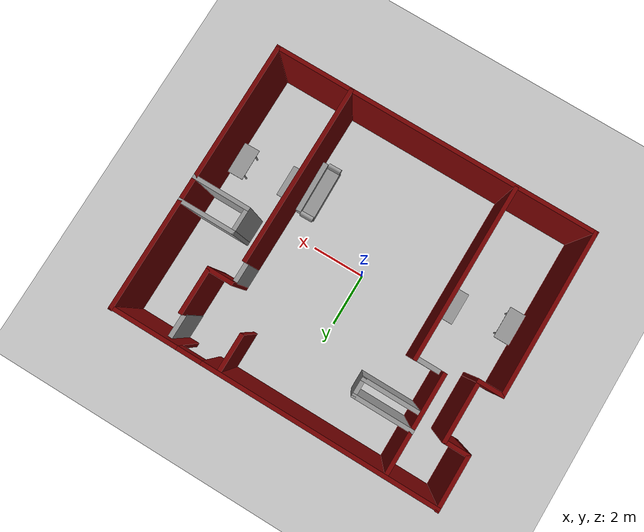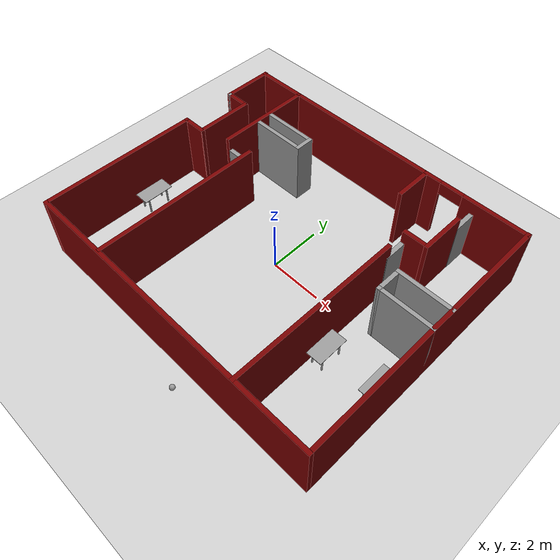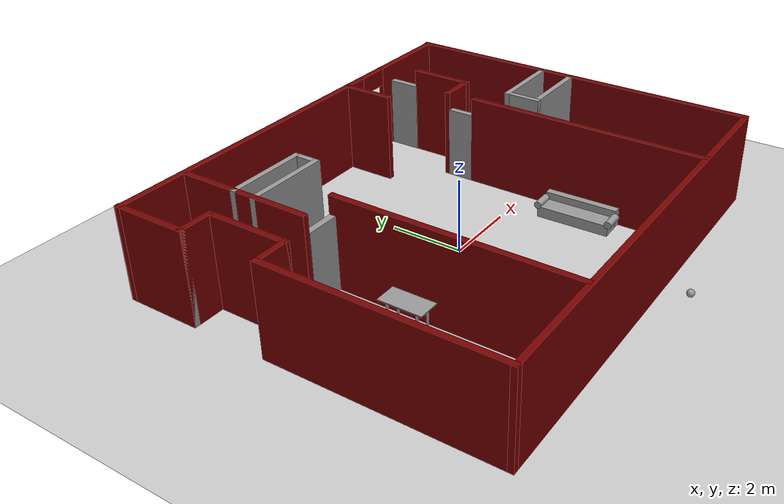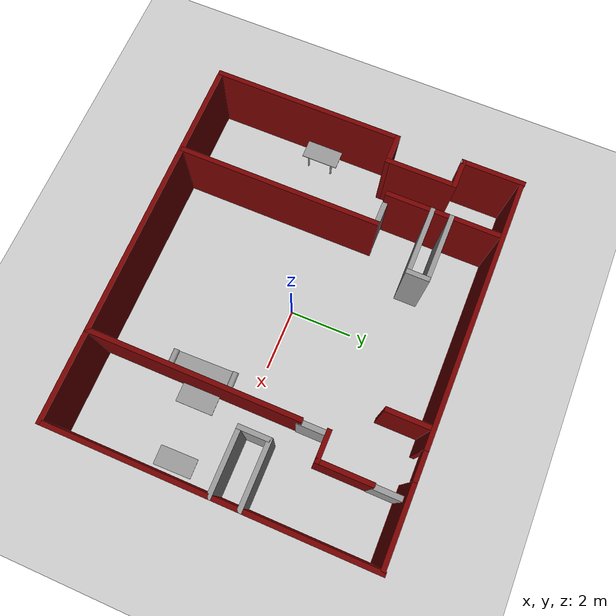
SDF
<sdf version="1.6">
 <world name="default">
  <plugin name="hello" filename="libhello.so"/>
  <light name="sun" type="directional">
   <pose>0 0 10 0 -0 0</pose>
   <diffuse>0.8 0.8 0.8 1</diffuse>
   <specular>0.2 0.2 0.2 1</specular>
   <attenuation>
    <range>1000</range>
    <constant>0.9</constant>
    <linear>0.01</linear>
    <quadratic>0.001</quadratic>
   </attenuation>
   <direction>-0.5 0.1 -0.9</direction>
  </light>
  <model name="ground_plane">
   <static>1</static>
   <link name="link">
    <collision name="collision">
     <geometry><plane><normal>0 0 1</normal><size>100 100</size></plane></geometry>
     <surface>
      <contact><collide_bitmask>65535</collide_bitmask></contact>
      <friction><ode><mu>100</mu><mu2>50</mu2></ode></friction>
     </surface>
    </collision>
    <visual name="visual">
     <cast_shadows>0</cast_shadows>
     <geometry><plane><normal>0 0 1</normal><size>100 100</size></plane></geometry>
     <material>
      <script><uri>file://media/materials/scripts/gazebo.material</uri><name>Gazebo/Grey</name></script>
     </material>
    </visual>
   </link>
  </model>
  <gravity>0 0 -9.8</gravity>
  <magnetic_field>6e-06 2.3e-05 -4.2e-05</magnetic_field>
  <atmosphere type="adiabatic"/>
  <physics name="default_physics" default="0" type="ode">
   <max_step_size>0.001</max_step_size>
   <real_time_factor>1</real_time_factor>
   <real_time_update_rate>1000</real_time_update_rate>
  </physics>
  <scene><ambient>0.4 0.4 0.4 1</ambient><background>0.7 0.7 0.7 1</background><shadows>1</shadows></scene>
  <spherical_coordinates>
   <surface_model>EARTH_WGS84</surface_model>
   <latitude_deg>0</latitude_deg>
   <longitude_deg>0</longitude_deg>
   <elevation>0</elevation>
   <heading_deg>0</heading_deg>
  </spherical_coordinates>
  <model name="my_apartment">
   <pose>0.207005 0.146028 0 0 -0 0</pose>
   <link name="Door_10">
    <collision name="Door_10_Collision">
     <geometry><box><size>0.9 0.17 2</size></box></geometry>
     <pose>0 0 1 0 -0 0</pose>
    </collision>
    <visual name="Door_10_Visual">
     <pose>0 0 1 0 -0 0</pose>
     <geometry><box><size>0.9 0.17 2</size></box></geometry>
     <material>
      <script><uri>file://media/materials/scripts/gazebo.material</uri><name>Gazebo/Grey</name></script>
     </material>
    </visual>
    <pose>4.02192 4.47846 0 0 -0 1.56904</pose>
   </link>
   <link name="Door_11">
    <collision name="Door_11_Collision">
     <geometry><box><size>0.9 0.17 2</size></box></geometry>
     <pose>0 0 1 0 -0 0</pose>
    </collision>
    <visual name="Door_11_Visual">
     <pose>0 0 1 0 -0 0</pose>
     <geometry><box><size>0.9 0.17 2</size></box></geometry>
     <material>
      <script><uri>file://media/materials/scripts/gazebo.material</uri><name>Gazebo/Grey</name></script>
     </material>
    </visual>
    <pose>3.18154 1.88515 0 0 -0 1.57142</pose>
   </link>
   <link name="Door_8">
    <collision name="Door_8_Collision">
     <geometry><box><size>0.9 0.17 2</size></box></geometry>
     <pose>0 0 1 0 -0 0</pose>
    </collision>
    <visual name="Door_8_Visual">
     <pose>0 0 1 0 -0 0</pose>
     <geometry><box><size>0.9 0.17 2</size></box></geometry>
     <material>
      <script><uri>file://media/materials/scripts/gazebo.material</uri><name>Gazebo/Grey</name></script>
     </material>
    </visual>
    <pose>-3.58991 1.37189 0 0 -0 0</pose>
   </link>
   <link name="Wall_40">
    <pose>0 5 0 0 -0 0</pose>
    <visual name="Wall_40_Visual_0">
     <pose>-1.71889 0 1.25 0 -0 0</pose>
     <geometry><box><size>8.71223 0.15 2.5</size></box></geometry>
     <material>
      <script><uri>file://media/materials/scripts/gazebo.material</uri><name>Gazebo/Grey</name></script>
      <ambient>0.47451 0 0 1</ambient>
     </material>
     <meta><layer>0</layer></meta>
    </visual>
    <collision name="Wall_40_Collision_0">
     <geometry><box><size>8.71223 0.15 2.5</size></box></geometry>
     <pose>-1.71889 0 1.25 0 -0 0</pose>
    </collision>
    <visual name="Wall_40_Visual_1">
     <pose>4.80611 0 1.25 0 -0 0</pose>
     <geometry><box><size>2.53777 0.15 2.5</size></box></geometry>
     <material>
      <script><uri>file://media/materials/scripts/gazebo.material</uri><name>Gazebo/Grey</name></script>
      <ambient>0.47451 0 0 1</ambient>
     </material>
     <meta><layer>0</layer></meta>
    </visual>
    <collision name="Wall_40_Collision_1">
     <geometry><box><size>2.53777 0.15 2.5</size></box></geometry>
     <pose>4.80611 0 1.25 0 -0 0</pose>
    </collision>
    <visual name="Wall_40_Visual_2">
     <pose>3.08723 0 2.25 0 -0 0</pose>
     <geometry><box><size>0.9 0.15 0.5</size></box></geometry>
     <material>
      <script><uri>file://media/materials/scripts/gazebo.material</uri><name>Gazebo/Grey</name></script>
      <ambient>0.47451 0 0 1</ambient>
     </material>
     <meta><layer>0</layer></meta>
    </visual>
    <collision name="Wall_40_Collision_2">
     <geometry><box><size>0.9 0.15 0.5</size></box></geometry>
     <pose>3.08723 0 2.25 0 -0 0</pose>
    </collision>
   </link>
   <link name="Wall_41">
    <collision name="Wall_41_Collision">
     <geometry><box><size>10.1957 0.15 2.5</size></box></geometry>
     <pose>0 0 1.25 0 -0 0</pose>
    </collision>
    <visual name="Wall_41_Visual">
     <pose>0 0 1.25 0 -0 0</pose>
     <geometry><box><size>10.1957 0.15 2.5</size></box></geometry>
     <material>
      <script><uri>file://media/materials/scripts/gazebo.material</uri><name>Gazebo/Grey</name></script>
      <ambient>0.458824 0 0 1</ambient>
     </material>
     <meta><layer>0</layer></meta>
    </visual>
    <pose>6 0 0 0 0 -1.5708</pose>
   </link>
   <link name="Wall_42">
    <collision name="Wall_42_Collision">
     <geometry><box><size>12.15 0.15 2.5</size></box></geometry>
     <pose>0 0 1.25 0 -0 0</pose>
    </collision>
    <visual name="Wall_42_Visual">
     <pose>0 0 1.25 0 -0 0</pose>
     <geometry><box><size>12.15 0.15 2.5</size></box></geometry>
     <material>
      <script><uri>file://media/materials/scripts/gazebo.material</uri><name>Gazebo/Grey</name></script>
      <ambient>0.47451 0 0 1</ambient>
     </material>
     <meta><layer>0</layer></meta>
    </visual>
    <pose>0 -5.02287 0 0 -0 3.14159</pose>
   </link>
   <link name="Wall_43">
    <collision name="Wall_43_Collision">
     <geometry><box><size>6.15 0.15 2.5</size></box></geometry>
     <pose>0 0 1.25 0 -0 0</pose>
    </collision>
    <visual name="Wall_43_Visual">
     <pose>0 0 1.25 0 -0 0</pose>
     <geometry><box><size>6.15 0.15 2.5</size></box></geometry>
     <material>
      <script><uri>file://media/materials/scripts/gazebo.material</uri><name>Gazebo/Grey</name></script>
      <ambient>0.47451 0 0 1</ambient>
     </material>
     <meta><layer>0</layer></meta>
    </visual>
    <pose>-6 -2.02287 0 0 -0 1.5708</pose>
   </link>
   <link name="Wall_45">
    <collision name="Wall_45_Collision">
     <geometry><box><size>2.04574 0.15 2.5</size></box></geometry>
     <pose>0 0 1.25 0 -0 0</pose>
    </collision>
    <visual name="Wall_45_Visual">
     <pose>0 0 1.25 0 -0 0</pose>
     <geometry><box><size>2.04574 0.15 2.5</size></box></geometry>
     <material>
      <script><uri>file://media/materials/scripts/gazebo.material</uri><name>Gazebo/Grey</name></script>
      <ambient>0.47451 0 0 1</ambient>
     </material>
     <meta><layer>0</layer></meta>
    </visual>
    <pose>-6 4.075 0 0 0 -1.5708</pose>
   </link>
   <link name="Wall_47">
    <collision name="Wall_47_Collision">
     <geometry><box><size>0.15 0.15 2.5</size></box></geometry>
     <pose>0 0 1.25 0 -0 0</pose>
    </collision>
    <visual name="Wall_47_Visual">
     <pose>0 0 1.25 0 -0 0</pose>
     <geometry><box><size>0.15 0.15 2.5</size></box></geometry>
     <material>
      <script><uri>file://media/materials/scripts/gazebo.material</uri><name>Gazebo/Grey</name></script>
      <ambient>1 1 1 1</ambient>
     </material>
     <meta><layer>0</layer></meta>
    </visual>
    <pose>-6 3.12713 0 0 -0 0</pose>
   </link>
   <link name="Wall_51">
    <collision name="Wall_51_Collision">
     <geometry><box><size>1 0.15 2.5</size></box></geometry>
     <pose>0 0 1.25 0 -0 0</pose>
    </collision>
    <visual name="Wall_51_Visual">
     <pose>0 0 1.25 0 -0 0</pose>
     <geometry><box><size>1 0.15 2.5</size></box></geometry>
     <material>
      <script><uri>file://media/materials/scripts/gazebo.material</uri><name>Gazebo/Grey</name></script>
      <ambient>0.47451 0 0 1</ambient>
     </material>
     <meta><layer>0</layer></meta>
    </visual>
    <pose>-5.575 3.12713 0 0 -0 0</pose>
   </link>
   <link name="Wall_52">
    <collision name="Wall_52_Collision">
     <geometry><box><size>2.3 0.15 2.5</size></box></geometry>
     <pose>0 0 1.25 0 -0 0</pose>
    </collision>
    <visual name="Wall_52_Visual">
     <pose>0 0 1.25 0 -0 0</pose>
     <geometry><box><size>2.3 0.15 2.5</size></box></geometry>
     <material>
      <script><uri>file://media/materials/scripts/gazebo.material</uri><name>Gazebo/Grey</name></script>
      <ambient>0.47451 0 0 1</ambient>
     </material>
     <meta><layer>0</layer></meta>
    </visual>
    <pose>-5.15 2.05213 0 0 0 -1.5708</pose>
   </link>
   <link name="Wall_54">
    <collision name="Wall_54_Collision">
     <geometry><box><size>1 0.15 2.5</size></box></geometry>
     <pose>0 0 1.25 0 -0 0</pose>
    </collision>
    <visual name="Wall_54_Visual">
     <pose>0 0 1.25 0 -0 0</pose>
     <geometry><box><size>1 0.15 2.5</size></box></geometry>
     <material>
      <script><uri>file://media/materials/scripts/gazebo.material</uri><name>Gazebo/Grey</name></script>
      <ambient>0.47451 0 0 1</ambient>
     </material>
     <meta><layer>0</layer></meta>
    </visual>
    <pose>-5.575 0.97713 0 0 -0 0</pose>
   </link>
   <link name="Wall_56">
    <collision name="Wall_56_Collision">
     <geometry><box><size>3.75 0.15 2.5</size></box></geometry>
     <pose>0 0 1.25 0 -0 0</pose>
    </collision>
    <visual name="Wall_56_Visual">
     <pose>0 0 1.25 0 -0 0</pose>
     <geometry><box><size>3.75 0.15 2.5</size></box></geometry>
     <material>
      <script><uri>file://media/materials/scripts/gazebo.material</uri><name>Gazebo/Grey</name></script>
      <ambient>0.47451 0 0 1</ambient>
     </material>
     <meta><layer>0</layer></meta>
    </visual>
    <pose>-4.10991 3.17189 0 0 0 -1.5708</pose>
   </link>
   <link name="Wall_58">
    <collision name="Wall_58_Collision">
     <geometry><box><size>2.25 0.15 2.5</size></box></geometry>
     <pose>0 0 1.25 0 -0 0</pose>
    </collision>
    <visual name="Wall_58_Visual">
     <pose>0 0 1.25 0 -0 0</pose>
     <geometry><box><size>2.25 0.15 2.5</size></box></geometry>
     <material>
      <script><uri>file://media/materials/scripts/gazebo.material</uri><name>Gazebo/Grey</name></script>
      <ambient>1 1 1 1</ambient>
     </material>
     <meta><layer>0</layer></meta>
    </visual>
    <pose>-3.05992 3.39189 0 0 -0 0</pose>
   </link>
   <link name="Wall_59">
    <collision name="Wall_59_Collision">
     <geometry><box><size>0.75 0.15 2.5</size></box></geometry>
     <pose>0 0 1.25 0 -0 0</pose>
    </collision>
    <visual name="Wall_59_Visual">
     <pose>0 0 1.25 0 -0 0</pose>
     <geometry><box><size>0.75 0.15 2.5</size></box></geometry>
     <material>
      <script><uri>file://media/materials/scripts/gazebo.material</uri><name>Gazebo/Grey</name></script>
      <ambient>1 1 1 1</ambient>
     </material>
     <meta><layer>0</layer></meta>
    </visual>
    <pose>-2.00991 3.09189 0 0 0 -1.5708</pose>
   </link>
   <link name="Wall_60">
    <collision name="Wall_60_Collision">
     <geometry><box><size>2.25 0.15 2.5</size></box></geometry>
     <pose>0 0 1.25 0 -0 0</pose>
    </collision>
    <visual name="Wall_60_Visual">
     <pose>0 0 1.25 0 -0 0</pose>
     <geometry><box><size>2.25 0.15 2.5</size></box></geometry>
     <material>
      <script><uri>file://media/materials/scripts/gazebo.material</uri><name>Gazebo/Grey</name></script>
      <ambient>1 1 1 1</ambient>
     </material>
     <meta><layer>0</layer></meta>
    </visual>
    <pose>-3.05992 2.79189 0 0 -0 3.14159</pose>
   </link>
   <link name="Wall_62">
    <collision name="Wall_62_Collision">
     <geometry><box><size>6.5 0.15 2.5</size></box></geometry>
     <pose>0 0 1.25 0 -0 0</pose>
    </collision>
    <visual name="Wall_62_Visual">
     <pose>0 0 1.25 0 -0 0</pose>
     <geometry><box><size>6.5 0.15 2.5</size></box></geometry>
     <material>
      <script><uri>file://media/materials/scripts/gazebo.material</uri><name>Gazebo/Grey</name></script>
      <ambient>0.47451 0 0 1</ambient>
     </material>
     <meta><layer>0</layer></meta>
    </visual>
    <pose>-3.076 -1.78087 0 0 0 -1.5708</pose>
   </link>
   <link name="Wall_64">
    <collision name="Wall_64_Collision">
     <geometry><box><size>1.5 0.15 2.5</size></box></geometry>
     <pose>0 0 1.25 0 -0 0</pose>
    </collision>
    <visual name="Wall_64_Visual">
     <pose>0 0 1.25 0 -0 0</pose>
     <geometry><box><size>1.5 0.15 2.5</size></box></geometry>
     <material>
      <script><uri>file://media/materials/scripts/gazebo.material</uri><name>Gazebo/Grey</name></script>
      <ambient>0.47451 0 0 1</ambient>
     </material>
     <meta><layer>0</layer></meta>
    </visual>
    <pose>2 4.31413 0 0 0 -1.5708</pose>
   </link>
   <link name="Wall_66">
    <collision name="Wall_66_Collision">
     <geometry><box><size>1.75 0.15 2.5</size></box></geometry>
     <pose>0 0 1.25 0 -0 0</pose>
    </collision>
    <visual name="Wall_66_Visual">
     <pose>0 0 1.25 0 -0 0</pose>
     <geometry><box><size>1.75 0.15 2.5</size></box></geometry>
     <material>
      <script><uri>file://media/materials/scripts/gazebo.material</uri><name>Gazebo/Grey</name></script>
      <ambient>0.47451 0 0 1</ambient>
     </material>
     <meta><layer>0</layer></meta>
    </visual>
    <pose>4.02154 3.18013 0 0 0 -1.5708</pose>
   </link>
   <link name="Wall_68">
    <collision name="Wall_68_Collision">
     <geometry><box><size>1 0.15 2.5</size></box></geometry>
     <pose>0 0 1.25 0 -0 0</pose>
    </collision>
    <visual name="Wall_68_Visual">
     <pose>0 0 1.25 0 -0 0</pose>
     <geometry><box><size>1 0.15 2.5</size></box></geometry>
     <material>
      <script><uri>file://media/materials/scripts/gazebo.material</uri><name>Gazebo/Grey</name></script>
      <ambient>0.47451 0 0 1</ambient>
     </material>
     <meta><layer>0</layer></meta>
    </visual>
    <pose>3.59653 2.38014 0 0 -0 3.14159</pose>
   </link>
   <link name="Wall_70">
    <collision name="Wall_70_Collision">
     <geometry><box><size>6.7 0.15 2.5</size></box></geometry>
     <pose>0 0 1.25 0 -0 0</pose>
    </collision>
    <visual name="Wall_70_Visual">
     <pose>0 0 1.25 0 -0 0</pose>
     <geometry><box><size>6.7 0.15 2.5</size></box></geometry>
     <material>
      <script><uri>file://media/materials/scripts/gazebo.material</uri><name>Gazebo/Grey</name></script>
      <ambient>0.458824 0 0 1</ambient>
     </material>
     <meta><layer>0</layer></meta>
    </visual>
    <pose>3.17 -1.74787 0 0 0 -1.5708</pose>
   </link>
   <link name="Wall_72">
    <collision name="Wall_72_Collision">
     <geometry><box><size>2.15 0.15 2.5</size></box></geometry>
     <pose>0 0 1.25 0 -0 0</pose>
    </collision>
    <visual name="Wall_72_Visual">
     <pose>0 0 1.25 0 -0 0</pose>
     <geometry><box><size>2.15 0.15 2.5</size></box></geometry>
     <material>
      <script><uri>file://media/materials/scripts/gazebo.material</uri><name>Gazebo/Grey</name></script>
      <ambient>1 1 1 1</ambient>
     </material>
     <meta><layer>0</layer></meta>
    </visual>
    <pose>5 0.97713 0 0 -0 3.14159</pose>
   </link>
   <link name="Wall_73">
    <collision name="Wall_73_Collision">
     <geometry><box><size>1.05 0.15 2.5</size></box></geometry>
     <pose>0 0 1.25 0 -0 0</pose>
    </collision>
    <visual name="Wall_73_Visual">
     <pose>0 0 1.25 0 -0 0</pose>
     <geometry><box><size>1.05 0.15 2.5</size></box></geometry>
     <material>
      <script><uri>file://media/materials/scripts/gazebo.material</uri><name>Gazebo/Grey</name></script>
      <ambient>1 1 1 1</ambient>
     </material>
     <meta><layer>0</layer></meta>
    </visual>
    <pose>4 0.52713 0 0 0 -1.5708</pose>
   </link>
   <link name="Wall_74">
    <collision name="Wall_74_Collision">
     <geometry><box><size>2.15 0.15 2.5</size></box></geometry>
     <pose>0 0 1.25 0 -0 0</pose>
    </collision>
    <visual name="Wall_74_Visual">
     <pose>0 0 1.25 0 -0 0</pose>
     <geometry><box><size>2.15 0.15 2.5</size></box></geometry>
     <material>
      <script><uri>file://media/materials/scripts/gazebo.material</uri><name>Gazebo/Grey</name></script>
      <ambient>1 1 1 1</ambient>
     </material>
     <meta><layer>0</layer></meta>
    </visual>
    <pose>5 0.07713 0 0 -0 0</pose>
   </link>
   <static>1</static>
  </model>
  <model name="couch">
   <link name="link_2">
    <pose>0 -0.0875 -0.115 0 -0 0</pose>
    <inertial>
     <mass>1</mass>
     <inertia>
      <ixx>0.166667</ixx>
      <ixy>0</ixy>
      <ixz>0</ixz>
      <iyy>0.166667</iyy>
      <iyz>0</iyz>
      <izz>0.166667</izz>
     </inertia>
    </inertial>
    <visual name="visual">
     <geometry><box><size>2 0.5 0.3</size></box></geometry>
     <material>
      <lighting>1</lighting>
      <script><uri>file://media/materials/scripts/gazebo.material</uri><name>Gazebo/Grey</name></script>
      <shader type="pixel"><normal_map>__default__</normal_map></shader>
      <ambient>0.3 0.3 0.3 1</ambient>
      <diffuse>0.7 0.7 0.7 1</diffuse>
      <specular>0.01 0.01 0.01 1</specular>
      <emissive>0 0 0 1</emissive>
     </material>
    </visual>
    <collision name="collision">
     <geometry><box><size>2 0.5 0.3</size></box></geometry>
     <surface>
      <friction>
       <ode><mu>1</mu><mu2>1</mu2><fdir1>0 0 0</fdir1><slip1>0</slip1><slip2>0</slip2></ode>
       <torsional>
        <coefficient>1</coefficient>
        <patch_radius>0</patch_radius>
        <surface_radius>0</surface_radius>
        <use_patch_radius>1</use_patch_radius>
        <ode><slip>0</slip></ode>
       </torsional>
      </friction>
      <bounce><restitution_coefficient>0</restitution_coefficient><threshold>1e+06</threshold></bounce>
      <contact>
       <collide_without_contact>0</collide_without_contact>
       <collide_without_contact_bitmask>1</collide_without_contact_bitmask>
       <collide_bitmask>1</collide_bitmask>
       <ode>
        <soft_cfm>0</soft_cfm>
        <soft_erp>0.2</soft_erp>
        <kp>1e+13</kp>
        <kd>1</kd>
        <max_vel>0.01</max_vel>
        <min_depth>0</min_depth>
       </ode>
       <bullet>
        <split_impulse>1</split_impulse>
        <split_impulse_penetration_threshold>-0.01</split_impulse_penetration_threshold>
        <soft_cfm>0</soft_cfm>
        <soft_erp>0.2</soft_erp>
        <kp>1e+13</kp>
        <kd>1</kd>
       </bullet>
      </contact>
     </surface>
    </collision>
   </link>
   <link name="link_3">
    <pose>0 0.2625 -0.015 0 -0 0</pose>
    <inertial>
     <mass>1</mass>
     <inertia>
      <ixx>0.166667</ixx>
      <ixy>0</ixy>
      <ixz>0</ixz>
      <iyy>0.166667</iyy>
      <iyz>0</iyz>
      <izz>0.166667</izz>
     </inertia>
    </inertial>
    <visual name="visual">
     <geometry><box><size>2 0.2 0.5</size></box></geometry>
     <material>
      <lighting>1</lighting>
      <script><uri>file://media/materials/scripts/gazebo.material</uri><name>Gazebo/Grey</name></script>
      <shader type="pixel"><normal_map>__default__</normal_map></shader>
      <ambient>0.3 0.3 0.3 1</ambient>
      <diffuse>0.7 0.7 0.7 1</diffuse>
      <specular>0.01 0.01 0.01 1</specular>
      <emissive>0 0 0 1</emissive>
     </material>
    </visual>
    <collision name="collision">
     <geometry><box><size>2 0.2 0.5</size></box></geometry>
     <surface>
      <friction>
       <ode><mu>1</mu><mu2>1</mu2><fdir1>0 0 0</fdir1><slip1>0</slip1><slip2>0</slip2></ode>
       <torsional>
        <coefficient>1</coefficient>
        <patch_radius>0</patch_radius>
        <surface_radius>0</surface_radius>
        <use_patch_radius>1</use_patch_radius>
        <ode><slip>0</slip></ode>
       </torsional>
      </friction>
      <bounce><restitution_coefficient>0</restitution_coefficient><threshold>1e+06</threshold></bounce>
      <contact>
       <collide_without_contact>0</collide_without_contact>
       <collide_without_contact_bitmask>1</collide_without_contact_bitmask>
       <collide_bitmask>1</collide_bitmask>
       <ode>
        <soft_cfm>0</soft_cfm>
        <soft_erp>0.2</soft_erp>
        <kp>1e+13</kp>
        <kd>1</kd>
        <max_vel>0.01</max_vel>
        <min_depth>0</min_depth>
       </ode>
       <bullet>
        <split_impulse>1</split_impulse>
        <split_impulse_penetration_threshold>-0.01</split_impulse_penetration_threshold>
        <soft_cfm>0</soft_cfm>
        <soft_erp>0.2</soft_erp>
        <kp>1e+13</kp>
        <kd>1</kd>
       </bullet>
      </contact>
     </surface>
    </collision>
   </link>
   <link name="link_4">
    <pose>1 -0.0875 0.065 1.5707 -0 0</pose>
    <inertial>
     <mass>1</mass>
     <inertia><ixx>0.145833</ixx><ixy>0</ixy><ixz>0</ixz><iyy>0.145833</iyy><iyz>0</iyz><izz>0.125</izz></inertia>
    </inertial>
    <visual name="visual">
     <geometry><cylinder><radius>0.1</radius><length>0.5</length></cylinder></geometry>
     <material>
      <lighting>1</lighting>
      <script><uri>file://media/materials/scripts/gazebo.material</uri><name>Gazebo/Grey</name></script>
      <shader type="pixel"><normal_map>__default__</normal_map></shader>
      <ambient>0.3 0.3 0.3 1</ambient>
      <diffuse>0.7 0.7 0.7 1</diffuse>
      <specular>0.01 0.01 0.01 1</specular>
      <emissive>0 0 0 1</emissive>
     </material>
    </visual>
    <collision name="collision">
     <geometry><cylinder><radius>0.1</radius><length>0.5</length></cylinder></geometry>
     <surface>
      <friction>
       <ode><mu>1</mu><mu2>1</mu2><fdir1>0 0 0</fdir1><slip1>0</slip1><slip2>0</slip2></ode>
       <torsional>
        <coefficient>1</coefficient>
        <patch_radius>0</patch_radius>
        <surface_radius>0</surface_radius>
        <use_patch_radius>1</use_patch_radius>
        <ode><slip>0</slip></ode>
       </torsional>
      </friction>
      <bounce><restitution_coefficient>0</restitution_coefficient><threshold>1e+06</threshold></bounce>
      <contact>
       <collide_without_contact>0</collide_without_contact>
       <collide_without_contact_bitmask>1</collide_without_contact_bitmask>
       <collide_bitmask>1</collide_bitmask>
       <ode>
        <soft_cfm>0</soft_cfm>
        <soft_erp>0.2</soft_erp>
        <kp>1e+13</kp>
        <kd>1</kd>
        <max_vel>0.01</max_vel>
        <min_depth>0</min_depth>
       </ode>
       <bullet>
        <split_impulse>1</split_impulse>
        <split_impulse_penetration_threshold>-0.01</split_impulse_penetration_threshold>
        <soft_cfm>0</soft_cfm>
        <soft_erp>0.2</soft_erp>
        <kp>1e+13</kp>
        <kd>1</kd>
       </bullet>
      </contact>
     </surface>
    </collision>
   </link>
   <link name="link_4_clone">
    <pose>-1 -0.0875 0.065 1.5707 -0 0</pose>
    <inertial>
     <mass>1</mass>
     <inertia><ixx>0.145833</ixx><ixy>0</ixy><ixz>0</ixz><iyy>0.145833</iyy><iyz>0</iyz><izz>0.125</izz></inertia>
    </inertial>
    <visual name="visual">
     <geometry><cylinder><radius>0.1</radius><length>0.5</length></cylinder></geometry>
     <material>
      <lighting>1</lighting>
      <script><uri>file://media/materials/scripts/gazebo.material</uri><name>Gazebo/Grey</name></script>
      <shader type="pixel"><normal_map>__default__</normal_map></shader>
      <ambient>0.3 0.3 0.3 1</ambient>
      <diffuse>0.7 0.7 0.7 1</diffuse>
      <specular>0.01 0.01 0.01 1</specular>
      <emissive>0 0 0 1</emissive>
     </material>
    </visual>
    <collision name="collision">
     <geometry><cylinder><radius>0.1</radius><length>0.5</length></cylinder></geometry>
     <surface>
      <friction>
       <ode><mu>1</mu><mu2>1</mu2><fdir1>0 0 0</fdir1><slip1>0</slip1><slip2>0</slip2></ode>
       <torsional>
        <coefficient>1</coefficient>
        <patch_radius>0</patch_radius>
        <surface_radius>0</surface_radius>
        <use_patch_radius>1</use_patch_radius>
        <ode><slip>0</slip></ode>
       </torsional>
      </friction>
      <bounce><restitution_coefficient>0</restitution_coefficient><threshold>1e+06</threshold></bounce>
      <contact>
       <collide_without_contact>0</collide_without_contact>
       <collide_without_contact_bitmask>1</collide_without_contact_bitmask>
       <collide_bitmask>1</collide_bitmask>
       <ode>
        <soft_cfm>0</soft_cfm>
        <soft_erp>0.2</soft_erp>
        <kp>1e+13</kp>
        <kd>1</kd>
        <max_vel>0.01</max_vel>
        <min_depth>0</min_depth>
       </ode>
       <bullet>
        <split_impulse>1</split_impulse>
        <split_impulse_penetration_threshold>-0.01</split_impulse_penetration_threshold>
        <soft_cfm>0</soft_cfm>
        <soft_erp>0.2</soft_erp>
        <kp>1e+13</kp>
        <kd>1</kd>
       </bullet>
      </contact>
     </surface>
    </collision>
   </link>
   <joint name="link_2_JOINT_4" type="fixed">
    <parent>link_2</parent>
    <child>link_4_clone</child>
    <physics>
     <ode><limit><cfm>0</cfm><erp>0.2</erp></limit><suspension><cfm>0</cfm><erp>0.2</erp></suspension></ode>
    </physics>
   </joint>
   <joint name="link_2_JOINT_6" type="fixed">
    <parent>link_2</parent>
    <child>link_3</child>
    <physics>
     <ode><limit><cfm>0</cfm><erp>0.2</erp></limit><suspension><cfm>0</cfm><erp>0.2</erp></suspension></ode>
    </physics>
   </joint>
   <joint name="link_2_JOINT_7" type="fixed">
    <parent>link_2</parent>
    <child>link_4</child>
    <physics>
     <ode><limit><cfm>0</cfm><erp>0.2</erp></limit><suspension><cfm>0</cfm><erp>0.2</erp></suspension></ode>
    </physics>
   </joint>
   <static>0</static>
   <pose>2.91014 -1.80114 0.265 1e-06 -0 -1.54803</pose>
  </model>
  <model name="desk_0">
   <link name="link_0">
    <pose>-0.4 -0.2 -0.068 0 -0 0</pose>
    <inertial>
     <mass>1</mass>
     <inertia><ixx>0.145833</ixx><ixy>0</ixy><ixz>0</ixz><iyy>0.145833</iyy><iyz>0</iyz><izz>0.125</izz></inertia>
    </inertial>
    <visual name="visual">
     <geometry><cylinder><radius>0.03</radius><length>0.67</length></cylinder></geometry>
     <material>
      <lighting>1</lighting>
      <script><uri>file://media/materials/scripts/gazebo.material</uri><name>Gazebo/Grey</name></script>
      <shader type="pixel"><normal_map>__default__</normal_map></shader>
      <ambient>0.3 0.3 0.3 1</ambient>
      <diffuse>0.7 0.7 0.7 1</diffuse>
      <specular>0.01 0.01 0.01 1</specular>
      <emissive>0 0 0 1</emissive>
     </material>
    </visual>
    <collision name="collision">
     <geometry><cylinder><radius>0.03</radius><length>0.67</length></cylinder></geometry>
     <surface>
      <friction>
       <ode><mu>1</mu><mu2>1</mu2><fdir1>0 0 0</fdir1><slip1>0</slip1><slip2>0</slip2></ode>
       <torsional>
        <coefficient>1</coefficient>
        <patch_radius>0</patch_radius>
        <surface_radius>0</surface_radius>
        <use_patch_radius>1</use_patch_radius>
        <ode><slip>0</slip></ode>
       </torsional>
      </friction>
      <bounce><restitution_coefficient>0</restitution_coefficient><threshold>1e+06</threshold></bounce>
      <contact>
       <collide_without_contact>0</collide_without_contact>
       <collide_without_contact_bitmask>1</collide_without_contact_bitmask>
       <collide_bitmask>1</collide_bitmask>
       <ode>
        <soft_cfm>0</soft_cfm>
        <soft_erp>0.2</soft_erp>
        <kp>1e+13</kp>
        <kd>1</kd>
        <max_vel>0.01</max_vel>
        <min_depth>0</min_depth>
       </ode>
       <bullet>
        <split_impulse>1</split_impulse>
        <split_impulse_penetration_threshold>-0.01</split_impulse_penetration_threshold>
        <soft_cfm>0</soft_cfm>
        <soft_erp>0.2</soft_erp>
        <kp>1e+13</kp>
        <kd>1</kd>
       </bullet>
      </contact>
     </surface>
    </collision>
   </link>
   <link name="link_0_clone">
    <pose>-0.4 0.2 -0.068 0 -0 0</pose>
    <inertial>
     <mass>1</mass>
     <inertia><ixx>0.145833</ixx><ixy>0</ixy><ixz>0</ixz><iyy>0.145833</iyy><iyz>0</iyz><izz>0.125</izz></inertia>
    </inertial>
    <visual name="visual">
     <geometry><cylinder><radius>0.03</radius><length>0.67</length></cylinder></geometry>
     <material>
      <lighting>1</lighting>
      <script><uri>file://media/materials/scripts/gazebo.material</uri><name>Gazebo/Grey</name></script>
      <shader type="pixel"><normal_map>__default__</normal_map></shader>
      <ambient>0.3 0.3 0.3 1</ambient>
      <diffuse>0.7 0.7 0.7 1</diffuse>
      <specular>0.01 0.01 0.01 1</specular>
      <emissive>0 0 0 1</emissive>
     </material>
    </visual>
    <collision name="collision">
     <geometry><cylinder><radius>0.03</radius><length>0.67</length></cylinder></geometry>
     <surface>
      <friction>
       <ode><mu>1</mu><mu2>1</mu2><fdir1>0 0 0</fdir1><slip1>0</slip1><slip2>0</slip2></ode>
       <torsional>
        <coefficient>1</coefficient>
        <patch_radius>0</patch_radius>
        <surface_radius>0</surface_radius>
        <use_patch_radius>1</use_patch_radius>
        <ode><slip>0</slip></ode>
       </torsional>
      </friction>
      <bounce><restitution_coefficient>0</restitution_coefficient><threshold>1e+06</threshold></bounce>
      <contact>
       <collide_without_contact>0</collide_without_contact>
       <collide_without_contact_bitmask>1</collide_without_contact_bitmask>
       <collide_bitmask>1</collide_bitmask>
       <ode>
        <soft_cfm>0</soft_cfm>
        <soft_erp>0.2</soft_erp>
        <kp>1e+13</kp>
        <kd>1</kd>
        <max_vel>0.01</max_vel>
        <min_depth>0</min_depth>
       </ode>
       <bullet>
        <split_impulse>1</split_impulse>
        <split_impulse_penetration_threshold>-0.01</split_impulse_penetration_threshold>
        <soft_cfm>0</soft_cfm>
        <soft_erp>0.2</soft_erp>
        <kp>1e+13</kp>
        <kd>1</kd>
       </bullet>
      </contact>
     </surface>
    </collision>
   </link>
   <link name="link_0_clone_0">
    <pose>0.4 0.2 -0.068 0 -0 0</pose>
    <inertial>
     <mass>1</mass>
     <inertia><ixx>0.145833</ixx><ixy>0</ixy><ixz>0</ixz><iyy>0.145833</iyy><iyz>0</iyz><izz>0.125</izz></inertia>
    </inertial>
    <visual name="visual">
     <geometry><cylinder><radius>0.03</radius><length>0.67</length></cylinder></geometry>
     <material>
      <lighting>1</lighting>
      <script><uri>file://media/materials/scripts/gazebo.material</uri><name>Gazebo/Grey</name></script>
      <shader type="pixel"><normal_map>__default__</normal_map></shader>
      <ambient>0.3 0.3 0.3 1</ambient>
      <diffuse>0.7 0.7 0.7 1</diffuse>
      <specular>0.01 0.01 0.01 1</specular>
      <emissive>0 0 0 1</emissive>
     </material>
    </visual>
    <collision name="collision">
     <geometry><cylinder><radius>0.03</radius><length>0.67</length></cylinder></geometry>
     <surface>
      <friction>
       <ode><mu>1</mu><mu2>1</mu2><fdir1>0 0 0</fdir1><slip1>0</slip1><slip2>0</slip2></ode>
       <torsional>
        <coefficient>1</coefficient>
        <patch_radius>0</patch_radius>
        <surface_radius>0</surface_radius>
        <use_patch_radius>1</use_patch_radius>
        <ode><slip>0</slip></ode>
       </torsional>
      </friction>
      <bounce><restitution_coefficient>0</restitution_coefficient><threshold>1e+06</threshold></bounce>
      <contact>
       <collide_without_contact>0</collide_without_contact>
       <collide_without_contact_bitmask>1</collide_without_contact_bitmask>
       <collide_bitmask>1</collide_bitmask>
       <ode>
        <soft_cfm>0</soft_cfm>
        <soft_erp>0.2</soft_erp>
        <kp>1e+13</kp>
        <kd>1</kd>
        <max_vel>0.01</max_vel>
        <min_depth>0</min_depth>
       </ode>
       <bullet>
        <split_impulse>1</split_impulse>
        <split_impulse_penetration_threshold>-0.01</split_impulse_penetration_threshold>
        <soft_cfm>0</soft_cfm>
        <soft_erp>0.2</soft_erp>
        <kp>1e+13</kp>
        <kd>1</kd>
       </bullet>
      </contact>
     </surface>
    </collision>
   </link>
   <link name="link_0_clone_1">
    <pose>0.4 -0.2 -0.068 0 -0 0</pose>
    <inertial>
     <mass>1</mass>
     <inertia><ixx>0.145833</ixx><ixy>0</ixy><ixz>0</ixz><iyy>0.145833</iyy><iyz>0</iyz><izz>0.125</izz></inertia>
    </inertial>
    <visual name="visual">
     <geometry><cylinder><radius>0.03</radius><length>0.67</length></cylinder></geometry>
     <material>
      <lighting>1</lighting>
      <script><uri>file://media/materials/scripts/gazebo.material</uri><name>Gazebo/Grey</name></script>
      <shader type="pixel"><normal_map>__default__</normal_map></shader>
      <ambient>0.3 0.3 0.3 1</ambient>
      <diffuse>0.7 0.7 0.7 1</diffuse>
      <specular>0.01 0.01 0.01 1</specular>
      <emissive>0 0 0 1</emissive>
     </material>
    </visual>
    <collision name="collision">
     <geometry><cylinder><radius>0.03</radius><length>0.67</length></cylinder></geometry>
     <surface>
      <friction>
       <ode><mu>1</mu><mu2>1</mu2><fdir1>0 0 0</fdir1><slip1>0</slip1><slip2>0</slip2></ode>
       <torsional>
        <coefficient>1</coefficient>
        <patch_radius>0</patch_radius>
        <surface_radius>0</surface_radius>
        <use_patch_radius>1</use_patch_radius>
        <ode><slip>0</slip></ode>
       </torsional>
      </friction>
      <bounce><restitution_coefficient>0</restitution_coefficient><threshold>1e+06</threshold></bounce>
      <contact>
       <collide_without_contact>0</collide_without_contact>
       <collide_without_contact_bitmask>1</collide_without_contact_bitmask>
       <collide_bitmask>1</collide_bitmask>
       <ode>
        <soft_cfm>0</soft_cfm>
        <soft_erp>0.2</soft_erp>
        <kp>1e+13</kp>
        <kd>1</kd>
        <max_vel>0.01</max_vel>
        <min_depth>0</min_depth>
       </ode>
       <bullet>
        <split_impulse>1</split_impulse>
        <split_impulse_penetration_threshold>-0.01</split_impulse_penetration_threshold>
        <soft_cfm>0</soft_cfm>
        <soft_erp>0.2</soft_erp>
        <kp>1e+13</kp>
        <kd>1</kd>
       </bullet>
      </contact>
     </surface>
    </collision>
   </link>
   <link name="link_1">
    <pose>0 0 0.272 0 -0 0</pose>
    <inertial>
     <mass>1</mass>
     <inertia>
      <ixx>0.166667</ixx>
      <ixy>0</ixy>
      <ixz>0</ixz>
      <iyy>0.166667</iyy>
      <iyz>0</iyz>
      <izz>0.166667</izz>
     </inertia>
    </inertial>
    <visual name="visual">
     <geometry><box><size>1.2 0.6 0.02</size></box></geometry>
     <material>
      <lighting>1</lighting>
      <script><uri>file://media/materials/scripts/gazebo.material</uri><name>Gazebo/Grey</name></script>
      <shader type="pixel"><normal_map>__default__</normal_map></shader>
      <ambient>0.3 0.3 0.3 1</ambient>
      <diffuse>0.7 0.7 0.7 1</diffuse>
      <specular>0.01 0.01 0.01 1</specular>
      <emissive>0 0 0 1</emissive>
     </material>
    </visual>
    <collision name="collision">
     <geometry><box><size>1.2 0.6 0.02</size></box></geometry>
     <surface>
      <friction>
       <ode><mu>1</mu><mu2>1</mu2><fdir1>0 0 0</fdir1><slip1>0</slip1><slip2>0</slip2></ode>
       <torsional>
        <coefficient>1</coefficient>
        <patch_radius>0</patch_radius>
        <surface_radius>0</surface_radius>
        <use_patch_radius>1</use_patch_radius>
        <ode><slip>0</slip></ode>
       </torsional>
      </friction>
      <bounce><restitution_coefficient>0</restitution_coefficient><threshold>1e+06</threshold></bounce>
      <contact>
       <collide_without_contact>0</collide_without_contact>
       <collide_without_contact_bitmask>1</collide_without_contact_bitmask>
       <collide_bitmask>1</collide_bitmask>
       <ode>
        <soft_cfm>0</soft_cfm>
        <soft_erp>0.2</soft_erp>
        <kp>1e+13</kp>
        <kd>1</kd>
        <max_vel>0.01</max_vel>
        <min_depth>0</min_depth>
       </ode>
       <bullet>
        <split_impulse>1</split_impulse>
        <split_impulse_penetration_threshold>-0.01</split_impulse_penetration_threshold>
        <soft_cfm>0</soft_cfm>
        <soft_erp>0.2</soft_erp>
        <kp>1e+13</kp>
        <kd>1</kd>
       </bullet>
      </contact>
     </surface>
    </collision>
   </link>
   <joint name="link_1_JOINT_0" type="fixed">
    <parent>link_1</parent>
    <child>link_0</child>
    <physics>
     <ode><limit><cfm>0</cfm><erp>0.2</erp></limit><suspension><cfm>0</cfm><erp>0.2</erp></suspension></ode>
    </physics>
   </joint>
   <joint name="link_1_JOINT_1" type="fixed">
    <parent>link_1</parent>
    <child>link_0_clone</child>
    <physics>
     <ode><limit><cfm>0</cfm><erp>0.2</erp></limit><suspension><cfm>0</cfm><erp>0.2</erp></suspension></ode>
    </physics>
   </joint>
   <joint name="link_1_JOINT_2" type="fixed">
    <parent>link_1</parent>
    <child>link_0_clone_0</child>
    <physics>
     <ode><limit><cfm>0</cfm><erp>0.2</erp></limit><suspension><cfm>0</cfm><erp>0.2</erp></suspension></ode>
    </physics>
   </joint>
   <joint name="link_1_JOINT_3" type="fixed">
    <parent>link_1</parent>
    <child>link_0_clone_1</child>
    <physics>
     <ode><limit><cfm>0</cfm><erp>0.2</erp></limit><suspension><cfm>0</cfm><erp>0.2</erp></suspension></ode>
    </physics>
   </joint>
   <static>0</static>
   <pose>5.71982 -1.30103 0.402999 -0 3e-06 -1.55465</pose>
  </model>
  <model name="desk_1">
   <link name="link_0">
    <pose>-0.4 -0.2 -0.068 0 -0 0</pose>
    <inertial>
     <mass>1</mass>
     <inertia><ixx>0.145833</ixx><ixy>0</ixy><ixz>0</ixz><iyy>0.145833</iyy><iyz>0</iyz><izz>0.125</izz></inertia>
    </inertial>
    <visual name="visual">
     <geometry><cylinder><radius>0.03</radius><length>0.67</length></cylinder></geometry>
     <material>
      <lighting>1</lighting>
      <script><uri>file://media/materials/scripts/gazebo.material</uri><name>Gazebo/Grey</name></script>
      <shader type="pixel"><normal_map>__default__</normal_map></shader>
      <ambient>0.3 0.3 0.3 1</ambient>
      <diffuse>0.7 0.7 0.7 1</diffuse>
      <specular>0.01 0.01 0.01 1</specular>
      <emissive>0 0 0 1</emissive>
     </material>
    </visual>
    <collision name="collision">
     <geometry><cylinder><radius>0.03</radius><length>0.67</length></cylinder></geometry>
     <surface>
      <friction>
       <ode><mu>1</mu><mu2>1</mu2><fdir1>0 0 0</fdir1><slip1>0</slip1><slip2>0</slip2></ode>
       <torsional>
        <coefficient>1</coefficient>
        <patch_radius>0</patch_radius>
        <surface_radius>0</surface_radius>
        <use_patch_radius>1</use_patch_radius>
        <ode><slip>0</slip></ode>
       </torsional>
      </friction>
      <bounce><restitution_coefficient>0</restitution_coefficient><threshold>1e+06</threshold></bounce>
      <contact>
       <collide_without_contact>0</collide_without_contact>
       <collide_without_contact_bitmask>1</collide_without_contact_bitmask>
       <collide_bitmask>1</collide_bitmask>
       <ode>
        <soft_cfm>0</soft_cfm>
        <soft_erp>0.2</soft_erp>
        <kp>1e+13</kp>
        <kd>1</kd>
        <max_vel>0.01</max_vel>
        <min_depth>0</min_depth>
       </ode>
       <bullet>
        <split_impulse>1</split_impulse>
        <split_impulse_penetration_threshold>-0.01</split_impulse_penetration_threshold>
        <soft_cfm>0</soft_cfm>
        <soft_erp>0.2</soft_erp>
        <kp>1e+13</kp>
        <kd>1</kd>
       </bullet>
      </contact>
     </surface>
    </collision>
   </link>
   <link name="link_0_clone">
    <pose>-0.4 0.2 -0.068 0 -0 0</pose>
    <inertial>
     <mass>1</mass>
     <inertia><ixx>0.145833</ixx><ixy>0</ixy><ixz>0</ixz><iyy>0.145833</iyy><iyz>0</iyz><izz>0.125</izz></inertia>
    </inertial>
    <visual name="visual">
     <geometry><cylinder><radius>0.03</radius><length>0.67</length></cylinder></geometry>
     <material>
      <lighting>1</lighting>
      <script><uri>file://media/materials/scripts/gazebo.material</uri><name>Gazebo/Grey</name></script>
      <shader type="pixel"><normal_map>__default__</normal_map></shader>
      <ambient>0.3 0.3 0.3 1</ambient>
      <diffuse>0.7 0.7 0.7 1</diffuse>
      <specular>0.01 0.01 0.01 1</specular>
      <emissive>0 0 0 1</emissive>
     </material>
    </visual>
    <collision name="collision">
     <geometry><cylinder><radius>0.03</radius><length>0.67</length></cylinder></geometry>
     <surface>
      <friction>
       <ode><mu>1</mu><mu2>1</mu2><fdir1>0 0 0</fdir1><slip1>0</slip1><slip2>0</slip2></ode>
       <torsional>
        <coefficient>1</coefficient>
        <patch_radius>0</patch_radius>
        <surface_radius>0</surface_radius>
        <use_patch_radius>1</use_patch_radius>
        <ode><slip>0</slip></ode>
       </torsional>
      </friction>
      <bounce><restitution_coefficient>0</restitution_coefficient><threshold>1e+06</threshold></bounce>
      <contact>
       <collide_without_contact>0</collide_without_contact>
       <collide_without_contact_bitmask>1</collide_without_contact_bitmask>
       <collide_bitmask>1</collide_bitmask>
       <ode>
        <soft_cfm>0</soft_cfm>
        <soft_erp>0.2</soft_erp>
        <kp>1e+13</kp>
        <kd>1</kd>
        <max_vel>0.01</max_vel>
        <min_depth>0</min_depth>
       </ode>
       <bullet>
        <split_impulse>1</split_impulse>
        <split_impulse_penetration_threshold>-0.01</split_impulse_penetration_threshold>
        <soft_cfm>0</soft_cfm>
        <soft_erp>0.2</soft_erp>
        <kp>1e+13</kp>
        <kd>1</kd>
       </bullet>
      </contact>
     </surface>
    </collision>
   </link>
   <link name="link_0_clone_0">
    <pose>0.4 0.2 -0.068 0 -0 0</pose>
    <inertial>
     <mass>1</mass>
     <inertia><ixx>0.145833</ixx><ixy>0</ixy><ixz>0</ixz><iyy>0.145833</iyy><iyz>0</iyz><izz>0.125</izz></inertia>
    </inertial>
    <visual name="visual">
     <geometry><cylinder><radius>0.03</radius><length>0.67</length></cylinder></geometry>
     <material>
      <lighting>1</lighting>
      <script><uri>file://media/materials/scripts/gazebo.material</uri><name>Gazebo/Grey</name></script>
      <shader type="pixel"><normal_map>__default__</normal_map></shader>
      <ambient>0.3 0.3 0.3 1</ambient>
      <diffuse>0.7 0.7 0.7 1</diffuse>
      <specular>0.01 0.01 0.01 1</specular>
      <emissive>0 0 0 1</emissive>
     </material>
    </visual>
    <collision name="collision">
     <geometry><cylinder><radius>0.03</radius><length>0.67</length></cylinder></geometry>
     <surface>
      <friction>
       <ode><mu>1</mu><mu2>1</mu2><fdir1>0 0 0</fdir1><slip1>0</slip1><slip2>0</slip2></ode>
       <torsional>
        <coefficient>1</coefficient>
        <patch_radius>0</patch_radius>
        <surface_radius>0</surface_radius>
        <use_patch_radius>1</use_patch_radius>
        <ode><slip>0</slip></ode>
       </torsional>
      </friction>
      <bounce><restitution_coefficient>0</restitution_coefficient><threshold>1e+06</threshold></bounce>
      <contact>
       <collide_without_contact>0</collide_without_contact>
       <collide_without_contact_bitmask>1</collide_without_contact_bitmask>
       <collide_bitmask>1</collide_bitmask>
       <ode>
        <soft_cfm>0</soft_cfm>
        <soft_erp>0.2</soft_erp>
        <kp>1e+13</kp>
        <kd>1</kd>
        <max_vel>0.01</max_vel>
        <min_depth>0</min_depth>
       </ode>
       <bullet>
        <split_impulse>1</split_impulse>
        <split_impulse_penetration_threshold>-0.01</split_impulse_penetration_threshold>
        <soft_cfm>0</soft_cfm>
        <soft_erp>0.2</soft_erp>
        <kp>1e+13</kp>
        <kd>1</kd>
       </bullet>
      </contact>
     </surface>
    </collision>
   </link>
   <link name="link_0_clone_1">
    <pose>0.4 -0.2 -0.068 0 -0 0</pose>
    <inertial>
     <mass>1</mass>
     <inertia><ixx>0.145833</ixx><ixy>0</ixy><ixz>0</ixz><iyy>0.145833</iyy><iyz>0</iyz><izz>0.125</izz></inertia>
    </inertial>
    <visual name="visual">
     <geometry><cylinder><radius>0.03</radius><length>0.67</length></cylinder></geometry>
     <material>
      <lighting>1</lighting>
      <script><uri>file://media/materials/scripts/gazebo.material</uri><name>Gazebo/Grey</name></script>
      <shader type="pixel"><normal_map>__default__</normal_map></shader>
      <ambient>0.3 0.3 0.3 1</ambient>
      <diffuse>0.7 0.7 0.7 1</diffuse>
      <specular>0.01 0.01 0.01 1</specular>
      <emissive>0 0 0 1</emissive>
     </material>
    </visual>
    <collision name="collision">
     <geometry><cylinder><radius>0.03</radius><length>0.67</length></cylinder></geometry>
     <surface>
      <friction>
       <ode><mu>1</mu><mu2>1</mu2><fdir1>0 0 0</fdir1><slip1>0</slip1><slip2>0</slip2></ode>
       <torsional>
        <coefficient>1</coefficient>
        <patch_radius>0</patch_radius>
        <surface_radius>0</surface_radius>
        <use_patch_radius>1</use_patch_radius>
        <ode><slip>0</slip></ode>
       </torsional>
      </friction>
      <bounce><restitution_coefficient>0</restitution_coefficient><threshold>1e+06</threshold></bounce>
      <contact>
       <collide_without_contact>0</collide_without_contact>
       <collide_without_contact_bitmask>1</collide_without_contact_bitmask>
       <collide_bitmask>1</collide_bitmask>
       <ode>
        <soft_cfm>0</soft_cfm>
        <soft_erp>0.2</soft_erp>
        <kp>1e+13</kp>
        <kd>1</kd>
        <max_vel>0.01</max_vel>
        <min_depth>0</min_depth>
       </ode>
       <bullet>
        <split_impulse>1</split_impulse>
        <split_impulse_penetration_threshold>-0.01</split_impulse_penetration_threshold>
        <soft_cfm>0</soft_cfm>
        <soft_erp>0.2</soft_erp>
        <kp>1e+13</kp>
        <kd>1</kd>
       </bullet>
      </contact>
     </surface>
    </collision>
   </link>
   <link name="link_1">
    <pose>0 0 0.272 0 -0 0</pose>
    <inertial>
     <mass>1</mass>
     <inertia>
      <ixx>0.166667</ixx>
      <ixy>0</ixy>
      <ixz>0</ixz>
      <iyy>0.166667</iyy>
      <iyz>0</iyz>
      <izz>0.166667</izz>
     </inertia>
    </inertial>
    <visual name="visual">
     <geometry><box><size>1.2 0.6 0.02</size></box></geometry>
     <material>
      <lighting>1</lighting>
      <script><uri>file://media/materials/scripts/gazebo.material</uri><name>Gazebo/Grey</name></script>
      <shader type="pixel"><normal_map>__default__</normal_map></shader>
      <ambient>0.3 0.3 0.3 1</ambient>
      <diffuse>0.7 0.7 0.7 1</diffuse>
      <specular>0.01 0.01 0.01 1</specular>
      <emissive>0 0 0 1</emissive>
     </material>
    </visual>
    <collision name="collision">
     <geometry><box><size>1.2 0.6 0.02</size></box></geometry>
     <surface>
      <friction>
       <ode><mu>1</mu><mu2>1</mu2><fdir1>0 0 0</fdir1><slip1>0</slip1><slip2>0</slip2></ode>
       <torsional>
        <coefficient>1</coefficient>
        <patch_radius>0</patch_radius>
        <surface_radius>0</surface_radius>
        <use_patch_radius>1</use_patch_radius>
        <ode><slip>0</slip></ode>
       </torsional>
      </friction>
      <bounce><restitution_coefficient>0</restitution_coefficient><threshold>1e+06</threshold></bounce>
      <contact>
       <collide_without_contact>0</collide_without_contact>
       <collide_without_contact_bitmask>1</collide_without_contact_bitmask>
       <collide_bitmask>1</collide_bitmask>
       <ode>
        <soft_cfm>0</soft_cfm>
        <soft_erp>0.2</soft_erp>
        <kp>1e+13</kp>
        <kd>1</kd>
        <max_vel>0.01</max_vel>
        <min_depth>0</min_depth>
       </ode>
       <bullet>
        <split_impulse>1</split_impulse>
        <split_impulse_penetration_threshold>-0.01</split_impulse_penetration_threshold>
        <soft_cfm>0</soft_cfm>
        <soft_erp>0.2</soft_erp>
        <kp>1e+13</kp>
        <kd>1</kd>
       </bullet>
      </contact>
     </surface>
    </collision>
   </link>
   <joint name="link_1_JOINT_0" type="fixed">
    <parent>link_1</parent>
    <child>link_0</child>
    <physics>
     <ode><limit><cfm>0</cfm><erp>0.2</erp></limit><suspension><cfm>0</cfm><erp>0.2</erp></suspension></ode>
    </physics>
   </joint>
   <joint name="link_1_JOINT_1" type="fixed">
    <parent>link_1</parent>
    <child>link_0_clone</child>
    <physics>
     <ode><limit><cfm>0</cfm><erp>0.2</erp></limit><suspension><cfm>0</cfm><erp>0.2</erp></suspension></ode>
    </physics>
   </joint>
   <joint name="link_1_JOINT_2" type="fixed">
    <parent>link_1</parent>
    <child>link_0_clone_0</child>
    <physics>
     <ode><limit><cfm>0</cfm><erp>0.2</erp></limit><suspension><cfm>0</cfm><erp>0.2</erp></suspension></ode>
    </physics>
   </joint>
   <joint name="link_1_JOINT_3" type="fixed">
    <parent>link_1</parent>
    <child>link_0_clone_1</child>
    <physics>
     <ode><limit><cfm>0</cfm><erp>0.2</erp></limit><suspension><cfm>0</cfm><erp>0.2</erp></suspension></ode>
    </physics>
   </joint>
   <static>0</static>
   <pose>-5.31819 -1.11527 0.402999 0 -2e-06 -1.5707</pose>
  </model>
  <model name="desk_2">
   <link name="link_0">
    <pose>-0.4 -0.2 -0.068 0 -0 0</pose>
    <inertial>
     <mass>1</mass>
     <inertia><ixx>0.145833</ixx><ixy>0</ixy><ixz>0</ixz><iyy>0.145833</iyy><iyz>0</iyz><izz>0.125</izz></inertia>
    </inertial>
    <visual name="visual">
     <geometry><cylinder><radius>0.03</radius><length>0.67</length></cylinder></geometry>
     <material>
      <lighting>1</lighting>
      <script><uri>file://media/materials/scripts/gazebo.material</uri><name>Gazebo/Grey</name></script>
      <shader type="pixel"><normal_map>__default__</normal_map></shader>
      <ambient>0.3 0.3 0.3 1</ambient>
      <diffuse>0.7 0.7 0.7 1</diffuse>
      <specular>0.01 0.01 0.01 1</specular>
      <emissive>0 0 0 1</emissive>
     </material>
    </visual>
    <collision name="collision">
     <geometry><cylinder><radius>0.03</radius><length>0.67</length></cylinder></geometry>
     <surface>
      <friction>
       <ode><mu>1</mu><mu2>1</mu2><fdir1>0 0 0</fdir1><slip1>0</slip1><slip2>0</slip2></ode>
       <torsional>
        <coefficient>1</coefficient>
        <patch_radius>0</patch_radius>
        <surface_radius>0</surface_radius>
        <use_patch_radius>1</use_patch_radius>
        <ode><slip>0</slip></ode>
       </torsional>
      </friction>
      <bounce><restitution_coefficient>0</restitution_coefficient><threshold>1e+06</threshold></bounce>
      <contact>
       <collide_without_contact>0</collide_without_contact>
       <collide_without_contact_bitmask>1</collide_without_contact_bitmask>
       <collide_bitmask>1</collide_bitmask>
       <ode>
        <soft_cfm>0</soft_cfm>
        <soft_erp>0.2</soft_erp>
        <kp>1e+13</kp>
        <kd>1</kd>
        <max_vel>0.01</max_vel>
        <min_depth>0</min_depth>
       </ode>
       <bullet>
        <split_impulse>1</split_impulse>
        <split_impulse_penetration_threshold>-0.01</split_impulse_penetration_threshold>
        <soft_cfm>0</soft_cfm>
        <soft_erp>0.2</soft_erp>
        <kp>1e+13</kp>
        <kd>1</kd>
       </bullet>
      </contact>
     </surface>
    </collision>
   </link>
   <link name="link_0_clone">
    <pose>-0.4 0.2 -0.068 0 -0 0</pose>
    <inertial>
     <mass>1</mass>
     <inertia><ixx>0.145833</ixx><ixy>0</ixy><ixz>0</ixz><iyy>0.145833</iyy><iyz>0</iyz><izz>0.125</izz></inertia>
    </inertial>
    <visual name="visual">
     <geometry><cylinder><radius>0.03</radius><length>0.67</length></cylinder></geometry>
     <material>
      <lighting>1</lighting>
      <script><uri>file://media/materials/scripts/gazebo.material</uri><name>Gazebo/Grey</name></script>
      <shader type="pixel"><normal_map>__default__</normal_map></shader>
      <ambient>0.3 0.3 0.3 1</ambient>
      <diffuse>0.7 0.7 0.7 1</diffuse>
      <specular>0.01 0.01 0.01 1</specular>
      <emissive>0 0 0 1</emissive>
     </material>
    </visual>
    <collision name="collision">
     <geometry><cylinder><radius>0.03</radius><length>0.67</length></cylinder></geometry>
     <surface>
      <friction>
       <ode><mu>1</mu><mu2>1</mu2><fdir1>0 0 0</fdir1><slip1>0</slip1><slip2>0</slip2></ode>
       <torsional>
        <coefficient>1</coefficient>
        <patch_radius>0</patch_radius>
        <surface_radius>0</surface_radius>
        <use_patch_radius>1</use_patch_radius>
        <ode><slip>0</slip></ode>
       </torsional>
      </friction>
      <bounce><restitution_coefficient>0</restitution_coefficient><threshold>1e+06</threshold></bounce>
      <contact>
       <collide_without_contact>0</collide_without_contact>
       <collide_without_contact_bitmask>1</collide_without_contact_bitmask>
       <collide_bitmask>1</collide_bitmask>
       <ode>
        <soft_cfm>0</soft_cfm>
        <soft_erp>0.2</soft_erp>
        <kp>1e+13</kp>
        <kd>1</kd>
        <max_vel>0.01</max_vel>
        <min_depth>0</min_depth>
       </ode>
       <bullet>
        <split_impulse>1</split_impulse>
        <split_impulse_penetration_threshold>-0.01</split_impulse_penetration_threshold>
        <soft_cfm>0</soft_cfm>
        <soft_erp>0.2</soft_erp>
        <kp>1e+13</kp>
        <kd>1</kd>
       </bullet>
      </contact>
     </surface>
    </collision>
   </link>
   <link name="link_0_clone_0">
    <pose>0.4 0.2 -0.068 0 -0 0</pose>
    <inertial>
     <mass>1</mass>
     <inertia><ixx>0.145833</ixx><ixy>0</ixy><ixz>0</ixz><iyy>0.145833</iyy><iyz>0</iyz><izz>0.125</izz></inertia>
    </inertial>
    <visual name="visual">
     <geometry><cylinder><radius>0.03</radius><length>0.67</length></cylinder></geometry>
     <material>
      <lighting>1</lighting>
      <script><uri>file://media/materials/scripts/gazebo.material</uri><name>Gazebo/Grey</name></script>
      <shader type="pixel"><normal_map>__default__</normal_map></shader>
      <ambient>0.3 0.3 0.3 1</ambient>
      <diffuse>0.7 0.7 0.7 1</diffuse>
      <specular>0.01 0.01 0.01 1</specular>
      <emissive>0 0 0 1</emissive>
     </material>
    </visual>
    <collision name="collision">
     <geometry><cylinder><radius>0.03</radius><length>0.67</length></cylinder></geometry>
     <surface>
      <friction>
       <ode><mu>1</mu><mu2>1</mu2><fdir1>0 0 0</fdir1><slip1>0</slip1><slip2>0</slip2></ode>
       <torsional>
        <coefficient>1</coefficient>
        <patch_radius>0</patch_radius>
        <surface_radius>0</surface_radius>
        <use_patch_radius>1</use_patch_radius>
        <ode><slip>0</slip></ode>
       </torsional>
      </friction>
      <bounce><restitution_coefficient>0</restitution_coefficient><threshold>1e+06</threshold></bounce>
      <contact>
       <collide_without_contact>0</collide_without_contact>
       <collide_without_contact_bitmask>1</collide_without_contact_bitmask>
       <collide_bitmask>1</collide_bitmask>
       <ode>
        <soft_cfm>0</soft_cfm>
        <soft_erp>0.2</soft_erp>
        <kp>1e+13</kp>
        <kd>1</kd>
        <max_vel>0.01</max_vel>
        <min_depth>0</min_depth>
       </ode>
       <bullet>
        <split_impulse>1</split_impulse>
        <split_impulse_penetration_threshold>-0.01</split_impulse_penetration_threshold>
        <soft_cfm>0</soft_cfm>
        <soft_erp>0.2</soft_erp>
        <kp>1e+13</kp>
        <kd>1</kd>
       </bullet>
      </contact>
     </surface>
    </collision>
   </link>
   <link name="link_0_clone_1">
    <pose>0.4 -0.2 -0.068 0 -0 0</pose>
    <inertial>
     <mass>1</mass>
     <inertia><ixx>0.145833</ixx><ixy>0</ixy><ixz>0</ixz><iyy>0.145833</iyy><iyz>0</iyz><izz>0.125</izz></inertia>
    </inertial>
    <visual name="visual">
     <geometry><cylinder><radius>0.03</radius><length>0.67</length></cylinder></geometry>
     <material>
      <lighting>1</lighting>
      <script><uri>file://media/materials/scripts/gazebo.material</uri><name>Gazebo/Grey</name></script>
      <shader type="pixel"><normal_map>__default__</normal_map></shader>
      <ambient>0.3 0.3 0.3 1</ambient>
      <diffuse>0.7 0.7 0.7 1</diffuse>
      <specular>0.01 0.01 0.01 1</specular>
      <emissive>0 0 0 1</emissive>
     </material>
    </visual>
    <collision name="collision">
     <geometry><cylinder><radius>0.03</radius><length>0.67</length></cylinder></geometry>
     <surface>
      <friction>
       <ode><mu>1</mu><mu2>1</mu2><fdir1>0 0 0</fdir1><slip1>0</slip1><slip2>0</slip2></ode>
       <torsional>
        <coefficient>1</coefficient>
        <patch_radius>0</patch_radius>
        <surface_radius>0</surface_radius>
        <use_patch_radius>1</use_patch_radius>
        <ode><slip>0</slip></ode>
       </torsional>
      </friction>
      <bounce><restitution_coefficient>0</restitution_coefficient><threshold>1e+06</threshold></bounce>
      <contact>
       <collide_without_contact>0</collide_without_contact>
       <collide_without_contact_bitmask>1</collide_without_contact_bitmask>
       <collide_bitmask>1</collide_bitmask>
       <ode>
        <soft_cfm>0</soft_cfm>
        <soft_erp>0.2</soft_erp>
        <kp>1e+13</kp>
        <kd>1</kd>
        <max_vel>0.01</max_vel>
        <min_depth>0</min_depth>
       </ode>
       <bullet>
        <split_impulse>1</split_impulse>
        <split_impulse_penetration_threshold>-0.01</split_impulse_penetration_threshold>
        <soft_cfm>0</soft_cfm>
        <soft_erp>0.2</soft_erp>
        <kp>1e+13</kp>
        <kd>1</kd>
       </bullet>
      </contact>
     </surface>
    </collision>
   </link>
   <link name="link_1">
    <pose>0 0 0.272 0 -0 0</pose>
    <inertial>
     <mass>1</mass>
     <inertia>
      <ixx>0.166667</ixx>
      <ixy>0</ixy>
      <ixz>0</ixz>
      <iyy>0.166667</iyy>
      <iyz>0</iyz>
      <izz>0.166667</izz>
     </inertia>
    </inertial>
    <visual name="visual">
     <geometry><box><size>1.2 0.6 0.02</size></box></geometry>
     <material>
      <lighting>1</lighting>
      <script><uri>file://media/materials/scripts/gazebo.material</uri><name>Gazebo/Grey</name></script>
      <shader type="pixel"><normal_map>__default__</normal_map></shader>
      <ambient>0.3 0.3 0.3 1</ambient>
      <diffuse>0.7 0.7 0.7 1</diffuse>
      <specular>0.01 0.01 0.01 1</specular>
      <emissive>0 0 0 1</emissive>
     </material>
    </visual>
    <collision name="collision">
     <geometry><box><size>1.2 0.6 0.02</size></box></geometry>
     <surface>
      <friction>
       <ode><mu>1</mu><mu2>1</mu2><fdir1>0 0 0</fdir1><slip1>0</slip1><slip2>0</slip2></ode>
       <torsional>
        <coefficient>1</coefficient>
        <patch_radius>0</patch_radius>
        <surface_radius>0</surface_radius>
        <use_patch_radius>1</use_patch_radius>
        <ode><slip>0</slip></ode>
       </torsional>
      </friction>
      <bounce><restitution_coefficient>0</restitution_coefficient><threshold>1e+06</threshold></bounce>
      <contact>
       <collide_without_contact>0</collide_without_contact>
       <collide_without_contact_bitmask>1</collide_without_contact_bitmask>
       <collide_bitmask>1</collide_bitmask>
       <ode>
        <soft_cfm>0</soft_cfm>
        <soft_erp>0.2</soft_erp>
        <kp>1e+13</kp>
        <kd>1</kd>
        <max_vel>0.01</max_vel>
        <min_depth>0</min_depth>
       </ode>
       <bullet>
        <split_impulse>1</split_impulse>
        <split_impulse_penetration_threshold>-0.01</split_impulse_penetration_threshold>
        <soft_cfm>0</soft_cfm>
        <soft_erp>0.2</soft_erp>
        <kp>1e+13</kp>
        <kd>1</kd>
       </bullet>
      </contact>
     </surface>
    </collision>
   </link>
   <joint name="link_1_JOINT_0" type="fixed">
    <parent>link_1</parent>
    <child>link_0</child>
    <physics>
     <ode><limit><cfm>0</cfm><erp>0.2</erp></limit><suspension><cfm>0</cfm><erp>0.2</erp></suspension></ode>
    </physics>
   </joint>
   <joint name="link_1_JOINT_1" type="fixed">
    <parent>link_1</parent>
    <child>link_0_clone</child>
    <physics>
     <ode><limit><cfm>0</cfm><erp>0.2</erp></limit><suspension><cfm>0</cfm><erp>0.2</erp></suspension></ode>
    </physics>
   </joint>
   <joint name="link_1_JOINT_2" type="fixed">
    <parent>link_1</parent>
    <child>link_0_clone_0</child>
    <physics>
     <ode><limit><cfm>0</cfm><erp>0.2</erp></limit><suspension><cfm>0</cfm><erp>0.2</erp></suspension></ode>
    </physics>
   </joint>
   <joint name="link_1_JOINT_3" type="fixed">
    <parent>link_1</parent>
    <child>link_0_clone_1</child>
    <physics>
     <ode><limit><cfm>0</cfm><erp>0.2</erp></limit><suspension><cfm>0</cfm><erp>0.2</erp></suspension></ode>
    </physics>
   </joint>
   <static>0</static>
   <pose>-3.2642 -0.722159 0.403 0 -2e-06 -1.5707</pose>
  </model>
  <model name="desk">
   <link name="link_0">
    <pose>-0.4 -0.2 -0.068 0 -0 0</pose>
    <inertial>
     <mass>1</mass>
     <inertia><ixx>0.145833</ixx><ixy>0</ixy><ixz>0</ixz><iyy>0.145833</iyy><iyz>0</iyz><izz>0.125</izz></inertia>
    </inertial>
    <visual name="visual">
     <geometry><cylinder><radius>0.03</radius><length>0.67</length></cylinder></geometry>
     <material>
      <lighting>1</lighting>
      <script><uri>file://media/materials/scripts/gazebo.material</uri><name>Gazebo/Grey</name></script>
      <shader type="pixel"><normal_map>__default__</normal_map></shader>
      <ambient>0.3 0.3 0.3 1</ambient>
      <diffuse>0.7 0.7 0.7 1</diffuse>
      <specular>0.01 0.01 0.01 1</specular>
      <emissive>0 0 0 1</emissive>
     </material>
    </visual>
    <collision name="collision">
     <geometry><cylinder><radius>0.03</radius><length>0.67</length></cylinder></geometry>
     <surface>
      <friction>
       <ode><mu>1</mu><mu2>1</mu2><fdir1>0 0 0</fdir1><slip1>0</slip1><slip2>0</slip2></ode>
       <torsional>
        <coefficient>1</coefficient>
        <patch_radius>0</patch_radius>
        <surface_radius>0</surface_radius>
        <use_patch_radius>1</use_patch_radius>
        <ode><slip>0</slip></ode>
       </torsional>
      </friction>
      <bounce><restitution_coefficient>0</restitution_coefficient><threshold>1e+06</threshold></bounce>
      <contact>
       <collide_without_contact>0</collide_without_contact>
       <collide_without_contact_bitmask>1</collide_without_contact_bitmask>
       <collide_bitmask>1</collide_bitmask>
       <ode>
        <soft_cfm>0</soft_cfm>
        <soft_erp>0.2</soft_erp>
        <kp>1e+13</kp>
        <kd>1</kd>
        <max_vel>0.01</max_vel>
        <min_depth>0</min_depth>
       </ode>
       <bullet>
        <split_impulse>1</split_impulse>
        <split_impulse_penetration_threshold>-0.01</split_impulse_penetration_threshold>
        <soft_cfm>0</soft_cfm>
        <soft_erp>0.2</soft_erp>
        <kp>1e+13</kp>
        <kd>1</kd>
       </bullet>
      </contact>
     </surface>
    </collision>
   </link>
   <link name="link_0_clone">
    <pose>-0.4 0.2 -0.068 0 -0 0</pose>
    <inertial>
     <mass>1</mass>
     <inertia><ixx>0.145833</ixx><ixy>0</ixy><ixz>0</ixz><iyy>0.145833</iyy><iyz>0</iyz><izz>0.125</izz></inertia>
    </inertial>
    <visual name="visual">
     <geometry><cylinder><radius>0.03</radius><length>0.67</length></cylinder></geometry>
     <material>
      <lighting>1</lighting>
      <script><uri>file://media/materials/scripts/gazebo.material</uri><name>Gazebo/Grey</name></script>
      <shader type="pixel"><normal_map>__default__</normal_map></shader>
      <ambient>0.3 0.3 0.3 1</ambient>
      <diffuse>0.7 0.7 0.7 1</diffuse>
      <specular>0.01 0.01 0.01 1</specular>
      <emissive>0 0 0 1</emissive>
     </material>
    </visual>
    <collision name="collision">
     <geometry><cylinder><radius>0.03</radius><length>0.67</length></cylinder></geometry>
     <surface>
      <friction>
       <ode><mu>1</mu><mu2>1</mu2><fdir1>0 0 0</fdir1><slip1>0</slip1><slip2>0</slip2></ode>
       <torsional>
        <coefficient>1</coefficient>
        <patch_radius>0</patch_radius>
        <surface_radius>0</surface_radius>
        <use_patch_radius>1</use_patch_radius>
        <ode><slip>0</slip></ode>
       </torsional>
      </friction>
      <bounce><restitution_coefficient>0</restitution_coefficient><threshold>1e+06</threshold></bounce>
      <contact>
       <collide_without_contact>0</collide_without_contact>
       <collide_without_contact_bitmask>1</collide_without_contact_bitmask>
       <collide_bitmask>1</collide_bitmask>
       <ode>
        <soft_cfm>0</soft_cfm>
        <soft_erp>0.2</soft_erp>
        <kp>1e+13</kp>
        <kd>1</kd>
        <max_vel>0.01</max_vel>
        <min_depth>0</min_depth>
       </ode>
       <bullet>
        <split_impulse>1</split_impulse>
        <split_impulse_penetration_threshold>-0.01</split_impulse_penetration_threshold>
        <soft_cfm>0</soft_cfm>
        <soft_erp>0.2</soft_erp>
        <kp>1e+13</kp>
        <kd>1</kd>
       </bullet>
      </contact>
     </surface>
    </collision>
   </link>
   <link name="link_0_clone_0">
    <pose>0.4 0.2 -0.068 0 -0 0</pose>
    <inertial>
     <mass>1</mass>
     <inertia><ixx>0.145833</ixx><ixy>0</ixy><ixz>0</ixz><iyy>0.145833</iyy><iyz>0</iyz><izz>0.125</izz></inertia>
    </inertial>
    <visual name="visual">
     <geometry><cylinder><radius>0.03</radius><length>0.67</length></cylinder></geometry>
     <material>
      <lighting>1</lighting>
      <script><uri>file://media/materials/scripts/gazebo.material</uri><name>Gazebo/Grey</name></script>
      <shader type="pixel"><normal_map>__default__</normal_map></shader>
      <ambient>0.3 0.3 0.3 1</ambient>
      <diffuse>0.7 0.7 0.7 1</diffuse>
      <specular>0.01 0.01 0.01 1</specular>
      <emissive>0 0 0 1</emissive>
     </material>
    </visual>
    <collision name="collision">
     <geometry><cylinder><radius>0.03</radius><length>0.67</length></cylinder></geometry>
     <surface>
      <friction>
       <ode><mu>1</mu><mu2>1</mu2><fdir1>0 0 0</fdir1><slip1>0</slip1><slip2>0</slip2></ode>
       <torsional>
        <coefficient>1</coefficient>
        <patch_radius>0</patch_radius>
        <surface_radius>0</surface_radius>
        <use_patch_radius>1</use_patch_radius>
        <ode><slip>0</slip></ode>
       </torsional>
      </friction>
      <bounce><restitution_coefficient>0</restitution_coefficient><threshold>1e+06</threshold></bounce>
      <contact>
       <collide_without_contact>0</collide_without_contact>
       <collide_without_contact_bitmask>1</collide_without_contact_bitmask>
       <collide_bitmask>1</collide_bitmask>
       <ode>
        <soft_cfm>0</soft_cfm>
        <soft_erp>0.2</soft_erp>
        <kp>1e+13</kp>
        <kd>1</kd>
        <max_vel>0.01</max_vel>
        <min_depth>0</min_depth>
       </ode>
       <bullet>
        <split_impulse>1</split_impulse>
        <split_impulse_penetration_threshold>-0.01</split_impulse_penetration_threshold>
        <soft_cfm>0</soft_cfm>
        <soft_erp>0.2</soft_erp>
        <kp>1e+13</kp>
        <kd>1</kd>
       </bullet>
      </contact>
     </surface>
    </collision>
   </link>
   <link name="link_0_clone_1">
    <pose>0.4 -0.2 -0.068 0 -0 0</pose>
    <inertial>
     <mass>1</mass>
     <inertia><ixx>0.145833</ixx><ixy>0</ixy><ixz>0</ixz><iyy>0.145833</iyy><iyz>0</iyz><izz>0.125</izz></inertia>
    </inertial>
    <visual name="visual">
     <geometry><cylinder><radius>0.03</radius><length>0.67</length></cylinder></geometry>
     <material>
      <lighting>1</lighting>
      <script><uri>file://media/materials/scripts/gazebo.material</uri><name>Gazebo/Grey</name></script>
      <shader type="pixel"><normal_map>__default__</normal_map></shader>
      <ambient>0.3 0.3 0.3 1</ambient>
      <diffuse>0.7 0.7 0.7 1</diffuse>
      <specular>0.01 0.01 0.01 1</specular>
      <emissive>0 0 0 1</emissive>
     </material>
    </visual>
    <collision name="collision">
     <geometry><cylinder><radius>0.03</radius><length>0.67</length></cylinder></geometry>
     <surface>
      <friction>
       <ode><mu>1</mu><mu2>1</mu2><fdir1>0 0 0</fdir1><slip1>0</slip1><slip2>0</slip2></ode>
       <torsional>
        <coefficient>1</coefficient>
        <patch_radius>0</patch_radius>
        <surface_radius>0</surface_radius>
        <use_patch_radius>1</use_patch_radius>
        <ode><slip>0</slip></ode>
       </torsional>
      </friction>
      <bounce><restitution_coefficient>0</restitution_coefficient><threshold>1e+06</threshold></bounce>
      <contact>
       <collide_without_contact>0</collide_without_contact>
       <collide_without_contact_bitmask>1</collide_without_contact_bitmask>
       <collide_bitmask>1</collide_bitmask>
       <ode>
        <soft_cfm>0</soft_cfm>
        <soft_erp>0.2</soft_erp>
        <kp>1e+13</kp>
        <kd>1</kd>
        <max_vel>0.01</max_vel>
        <min_depth>0</min_depth>
       </ode>
       <bullet>
        <split_impulse>1</split_impulse>
        <split_impulse_penetration_threshold>-0.01</split_impulse_penetration_threshold>
        <soft_cfm>0</soft_cfm>
        <soft_erp>0.2</soft_erp>
        <kp>1e+13</kp>
        <kd>1</kd>
       </bullet>
      </contact>
     </surface>
    </collision>
   </link>
   <link name="link_1">
    <pose>0 0 0.272 0 -0 0</pose>
    <inertial>
     <mass>1</mass>
     <inertia>
      <ixx>0.166667</ixx>
      <ixy>0</ixy>
      <ixz>0</ixz>
      <iyy>0.166667</iyy>
      <iyz>0</iyz>
      <izz>0.166667</izz>
     </inertia>
    </inertial>
    <visual name="visual">
     <geometry><box><size>1.2 0.6 0.02</size></box></geometry>
     <material>
      <lighting>1</lighting>
      <script><uri>file://media/materials/scripts/gazebo.material</uri><name>Gazebo/Grey</name></script>
      <shader type="pixel"><normal_map>__default__</normal_map></shader>
      <ambient>0.3 0.3 0.3 1</ambient>
      <diffuse>0.7 0.7 0.7 1</diffuse>
      <specular>0.01 0.01 0.01 1</specular>
      <emissive>0 0 0 1</emissive>
     </material>
    </visual>
    <collision name="collision">
     <geometry><box><size>1.2 0.6 0.02</size></box></geometry>
     <surface>
      <friction>
       <ode><mu>1</mu><mu2>1</mu2><fdir1>0 0 0</fdir1><slip1>0</slip1><slip2>0</slip2></ode>
       <torsional>
        <coefficient>1</coefficient>
        <patch_radius>0</patch_radius>
        <surface_radius>0</surface_radius>
        <use_patch_radius>1</use_patch_radius>
        <ode><slip>0</slip></ode>
       </torsional>
      </friction>
      <bounce><restitution_coefficient>0</restitution_coefficient><threshold>1e+06</threshold></bounce>
      <contact>
       <collide_without_contact>0</collide_without_contact>
       <collide_without_contact_bitmask>1</collide_without_contact_bitmask>
       <collide_bitmask>1</collide_bitmask>
       <ode>
        <soft_cfm>0</soft_cfm>
        <soft_erp>0.2</soft_erp>
        <kp>1e+13</kp>
        <kd>1</kd>
        <max_vel>0.01</max_vel>
        <min_depth>0</min_depth>
       </ode>
       <bullet>
        <split_impulse>1</split_impulse>
        <split_impulse_penetration_threshold>-0.01</split_impulse_penetration_threshold>
        <soft_cfm>0</soft_cfm>
        <soft_erp>0.2</soft_erp>
        <kp>1e+13</kp>
        <kd>1</kd>
       </bullet>
      </contact>
     </surface>
    </collision>
   </link>
   <joint name="link_1_JOINT_0" type="fixed">
    <parent>link_1</parent>
    <child>link_0</child>
    <physics>
     <ode><limit><cfm>0</cfm><erp>0.2</erp></limit><suspension><cfm>0</cfm><erp>0.2</erp></suspension></ode>
    </physics>
   </joint>
   <joint name="link_1_JOINT_1" type="fixed">
    <parent>link_1</parent>
    <child>link_0_clone</child>
    <physics>
     <ode><limit><cfm>0</cfm><erp>0.2</erp></limit><suspension><cfm>0</cfm><erp>0.2</erp></suspension></ode>
    </physics>
   </joint>
   <joint name="link_1_JOINT_2" type="fixed">
    <parent>link_1</parent>
    <child>link_0_clone_0</child>
    <physics>
     <ode><limit><cfm>0</cfm><erp>0.2</erp></limit><suspension><cfm>0</cfm><erp>0.2</erp></suspension></ode>
    </physics>
   </joint>
   <joint name="link_1_JOINT_3" type="fixed">
    <parent>link_1</parent>
    <child>link_0_clone_1</child>
    <physics>
     <ode><limit><cfm>0</cfm><erp>0.2</erp></limit><suspension><cfm>0</cfm><erp>0.2</erp></suspension></ode>
    </physics>
   </joint>
   <static>0</static>
   <pose>3.7858 -1.48678 0.403 -1e-06 -1e-06 -1.56077</pose>
  </model>
  <model name="my_ball">
   <link name="link_0">
    <inertial>
     <mass>1</mass>
     <inertia><ixx>0.1</ixx><ixy>0</ixy><ixz>0</ixz><iyy>0.1</iyy><iyz>0</iyz><izz>0.1</izz></inertia>
    </inertial>
    <visual name="visual">
     <geometry><sphere><radius>0.1</radius></sphere></geometry>
     <material>
      <lighting>1</lighting>
      <script><uri>file://media/materials/scripts/gazebo.material</uri><name>Gazebo/Grey</name></script>
      <shader type="pixel"><normal_map>__default__</normal_map></shader>
      <ambient>1 1 1 1</ambient>
      <diffuse>1 1 1 1</diffuse>
      <specular>1 1 1 1</specular>
      <emissive>1 1 1 1</emissive>
     </material>
    </visual>
    <collision name="collision">
     <geometry><sphere><radius>0.1</radius></sphere></geometry>
     <surface>
      <friction>
       <ode><mu>1</mu><mu2>1</mu2><fdir1>0 0 0</fdir1><slip1>0</slip1><slip2>0</slip2></ode>
       <torsional>
        <coefficient>1</coefficient>
        <patch_radius>0</patch_radius>
        <surface_radius>0</surface_radius>
        <use_patch_radius>1</use_patch_radius>
        <ode><slip>0</slip></ode>
       </torsional>
      </friction>
      <bounce><restitution_coefficient>0</restitution_coefficient><threshold>1e+06</threshold></bounce>
      <contact>
       <collide_without_contact>0</collide_without_contact>
       <collide_without_contact_bitmask>1</collide_without_contact_bitmask>
       <collide_bitmask>1</collide_bitmask>
       <ode>
        <soft_cfm>0</soft_cfm>
        <soft_erp>0.2</soft_erp>
        <kp>1e+13</kp>
        <kd>1</kd>
        <max_vel>0.01</max_vel>
        <min_depth>0</min_depth>
       </ode>
       <bullet>
        <split_impulse>1</split_impulse>
        <split_impulse_penetration_threshold>-0.01</split_impulse_penetration_threshold>
        <soft_cfm>0</soft_cfm>
        <soft_erp>0.2</soft_erp>
        <kp>1e+13</kp>
        <kd>1</kd>
       </bullet>
      </contact>
     </surface>
    </collision>
   </link>
   <static>0</static>
   <pose>1.22906 -5.59218 0.1 0 -0 0</pose>
  </model>
 </world>
</sdf>
